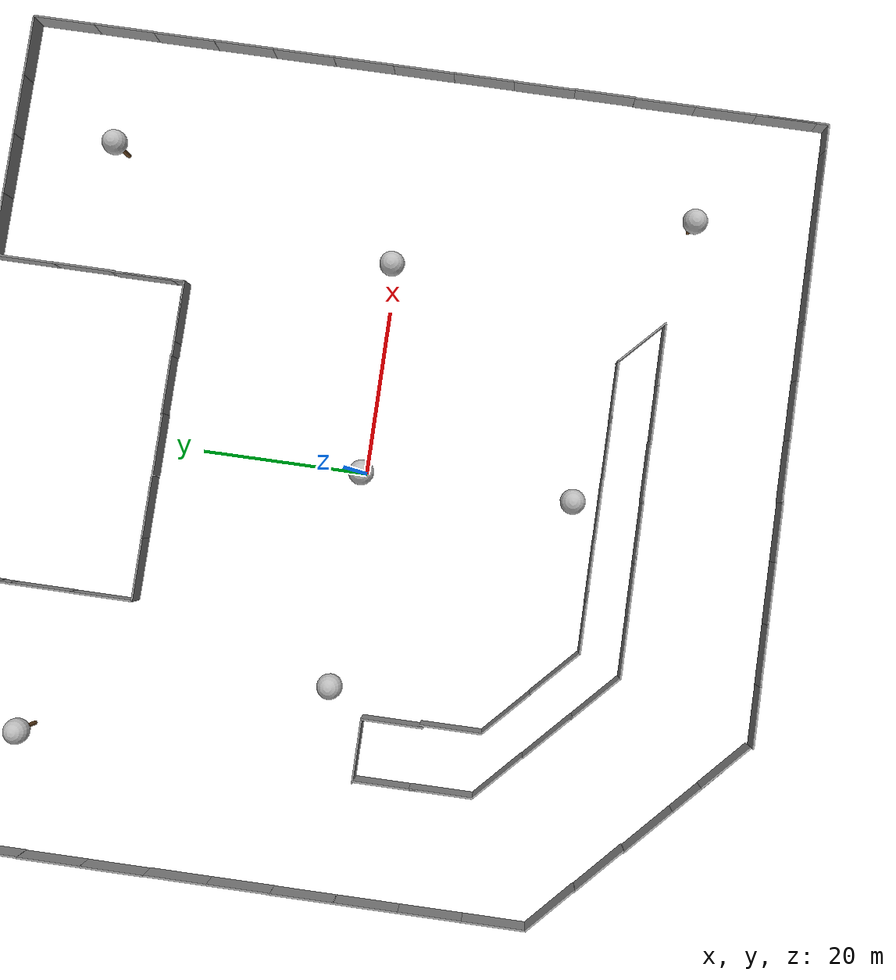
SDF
<sdf version="1.6">
 <world name="default">
  <plugin name="mrs_gazebo_static_transform_republisher_plugin" filename="libMRSGazeboStaticTransformRepublisher.so"/>
  <spherical_coordinates>
   <surface_model>EARTH_WGS84</surface_model>
   <latitude_deg>47.397743</latitude_deg>
   <longitude_deg>8.545594</longitude_deg>
   <elevation>0.0</elevation>
   <heading_deg>0</heading_deg>
  </spherical_coordinates>
  <physics name="default_physics" default="0" type="ode">
   <ode>
    <solver>
     <type>quick</type>
     <iters>10</iters>
     <sor>1.3</sor>
     <use_dynamic_moi_rescaling>0</use_dynamic_moi_rescaling>
    </solver>
    <constraints>
     <cfm>0</cfm>
     <erp>0.2</erp>
     <contact_max_correcting_vel>1000</contact_max_correcting_vel>
     <contact_surface_layer>0.001</contact_surface_layer>
    </constraints>
   </ode>
   <max_step_size>0.004</max_step_size>
   <real_time_factor>1</real_time_factor>
   <real_time_update_rate>250</real_time_update_rate>
  </physics>
  <scene><shadows>false</shadows></scene>
  <light type="directional" name="sun">
   <pose>250 250 600 0 0 0</pose>
   <diffuse>0.8 0.8 0.8 1</diffuse>
   <specular>0.2 0.2 0.2 1</specular>
   <attenuation>
    <range>1000</range>
    <constant>0.9</constant>
    <linear>0.01</linear>
    <quadratic>0.001</quadratic>
   </attenuation>
   <direction>0 0 -1</direction>
  </light>
  <model name="the_void">
   <static>1</static>
   <link name="link">
    <pose>0 0 0.1 0 -0 0</pose>
    <visual name="the_void">
     <pose>0 0 2 0 -0 0</pose>
     <geometry><sphere><radius>0.25</radius></sphere></geometry>
     <material>
      <script><uri>file://media/materials/scripts/Gazebo.material</uri><name>Gazebo/Black</name></script>
     </material>
    </visual>
   </link>
   <pose>-1000 -1000 0 0 -0 0</pose>
  </model>
  <plugin name="rviz_cam_synchronizer" filename="librviz_cam_synchronizer.so">
   <target_frame_id>gazebo_user_camera</target_frame_id>
   <world_origin_frame_id>uav1/gps_origin</world_origin_frame_id>
   <gazebo_camera_pose_topic>~/user_camera/pose</gazebo_camera_pose_topic>
   <target_frame_id>uav1::base_link</target_frame_id>
  </plugin>
  <gravity>0 0 -9.8066</gravity>
  <magnetic_field>6e-06 2.3e-05 -4.2e-05</magnetic_field>
  <atmosphere type="adiabatic"/>
  <model name="grey_wall">
   <static>1</static>
   <link name="link">
    <pose>0 0 1.4 0 -0 0</pose>
    <collision name="collision"><geometry><box><size>7.5 0.2 2.8</size></box></geometry></collision>
    <visual name="visual">
     <cast_shadows>0</cast_shadows>
     <geometry><box><size>7.5 0.2 2.8</size></box></geometry>
     <material>
      <script>
       <uri>model://grey_wall/materials/scripts</uri>
       <uri>model://grey_wall/materials/textures</uri>
       <name>vrc/grey_wall</name>
      </script>
     </material>
    </visual>
   </link>
   <pose>0 -50 0 0 -0 0</pose>
  </model>
  <model name="grey_wall_0">
   <static>1</static>
   <link name="link">
    <pose>0 0 1.4 0 -0 0</pose>
    <collision name="collision"><geometry><box><size>7.5 0.2 2.8</size></box></geometry></collision>
    <visual name="visual">
     <cast_shadows>0</cast_shadows>
     <geometry><box><size>7.5 0.2 2.8</size></box></geometry>
     <material>
      <script>
       <uri>model://grey_wall/materials/scripts</uri>
       <uri>model://grey_wall/materials/textures</uri>
       <name>vrc/grey_wall</name>
      </script>
     </material>
    </visual>
   </link>
   <pose>0 25 0 0 -0 0</pose>
  </model>
  <model name="grey_wall_1">
   <static>1</static>
   <link name="link">
    <pose>0 0 1.4 0 -0 0</pose>
    <collision name="collision"><geometry><box><size>7.5 0.2 2.8</size></box></geometry></collision>
    <visual name="visual">
     <cast_shadows>0</cast_shadows>
     <geometry><box><size>7.5 0.2 2.8</size></box></geometry>
     <material>
      <script>
       <uri>model://grey_wall/materials/scripts</uri>
       <uri>model://grey_wall/materials/textures</uri>
       <name>vrc/grey_wall</name>
      </script>
     </material>
    </visual>
   </link>
   <pose>50 0 0 0 -0 1.57</pose>
  </model>
  <model name="grey_wall_1_clone">
   <static>1</static>
   <link name="link">
    <pose>0 0 1.4 0 -0 0</pose>
    <collision name="collision"><geometry><box><size>7.5 0.2 2.8</size></box></geometry></collision>
    <visual name="visual">
     <cast_shadows>0</cast_shadows>
     <geometry><box><size>7.5 0.2 2.8</size></box></geometry>
     <material>
      <script>
       <uri>model://grey_wall/materials/scripts</uri>
       <uri>model://grey_wall/materials/textures</uri>
       <name>vrc/grey_wall</name>
      </script>
     </material>
    </visual>
   </link>
   <pose>-50 0 0 0 -0 1.57</pose>
  </model>
  <model name="grey_wall_1_clone_clone">
   <static>1</static>
   <link name="link">
    <pose>0 0 1.4 0 -0 0</pose>
    <collision name="collision"><geometry><box><size>7.5 0.2 2.8</size></box></geometry></collision>
    <visual name="visual">
     <cast_shadows>0</cast_shadows>
     <geometry><box><size>7.5 0.2 2.8</size></box></geometry>
     <material>
      <script>
       <uri>model://grey_wall/materials/scripts</uri>
       <uri>model://grey_wall/materials/textures</uri>
       <name>vrc/grey_wall</name>
      </script>
     </material>
    </visual>
   </link>
   <pose>-50.0069 -7.58109 0 0 -0 1.57</pose>
  </model>
  <model name="grey_wall_1_clone_clone_0">
   <static>1</static>
   <link name="link">
    <pose>0 0 1.4 0 -0 0</pose>
    <collision name="collision"><geometry><box><size>7.5 0.2 2.8</size></box></geometry></collision>
    <visual name="visual">
     <cast_shadows>0</cast_shadows>
     <geometry><box><size>7.5 0.2 2.8</size></box></geometry>
     <material>
      <script>
       <uri>model://grey_wall/materials/scripts</uri>
       <uri>model://grey_wall/materials/textures</uri>
       <name>vrc/grey_wall</name>
      </script>
     </material>
    </visual>
   </link>
   <pose>-50.0101 -15.0734 0 0 -0 1.57</pose>
  </model>
  <model name="grey_wall_1_clone_clone_1">
   <static>1</static>
   <link name="link">
    <pose>0 0 1.4 0 -0 0</pose>
    <collision name="collision"><geometry><box><size>7.5 0.2 2.8</size></box></geometry></collision>
    <visual name="visual">
     <cast_shadows>0</cast_shadows>
     <geometry><box><size>7.5 0.2 2.8</size></box></geometry>
     <material>
      <script>
       <uri>model://grey_wall/materials/scripts</uri>
       <uri>model://grey_wall/materials/textures</uri>
       <name>vrc/grey_wall</name>
      </script>
     </material>
    </visual>
   </link>
   <pose>-50.0164 -22.5285 0 0 -0 1.57</pose>
  </model>
  <model name="grey_wall_1_clone_clone_5">
   <static>1</static>
   <link name="link">
    <pose>0 0 1.4 0 -0 0</pose>
    <collision name="collision"><geometry><box><size>7.5 0.2 2.8</size></box></geometry></collision>
    <visual name="visual">
     <cast_shadows>0</cast_shadows>
     <geometry><box><size>7.5 0.2 2.8</size></box></geometry>
     <material>
      <script>
       <uri>model://grey_wall/materials/scripts</uri>
       <uri>model://grey_wall/materials/textures</uri>
       <name>vrc/grey_wall</name>
      </script>
     </material>
    </visual>
   </link>
   <pose>-49.9698 7.44842 0 0 -0 1.57</pose>
  </model>
  <model name="grey_wall_1_clone_clone_6">
   <static>1</static>
   <link name="link">
    <pose>0 0 1.4 0 -0 0</pose>
    <collision name="collision"><geometry><box><size>7.5 0.2 2.8</size></box></geometry></collision>
    <visual name="visual">
     <cast_shadows>0</cast_shadows>
     <geometry><box><size>7.5 0.2 2.8</size></box></geometry>
     <material>
      <script>
       <uri>model://grey_wall/materials/scripts</uri>
       <uri>model://grey_wall/materials/textures</uri>
       <name>vrc/grey_wall</name>
      </script>
     </material>
    </visual>
   </link>
   <pose>-49.9652 14.8689 0 0 -0 1.57</pose>
  </model>
  <model name="grey_wall_1_clone_clone_7">
   <static>1</static>
   <link name="link">
    <pose>0 0 1.4 0 -0 0</pose>
    <collision name="collision"><geometry><box><size>7.5 0.2 2.8</size></box></geometry></collision>
    <visual name="visual">
     <cast_shadows>0</cast_shadows>
     <geometry><box><size>7.5 0.2 2.8</size></box></geometry>
     <material>
      <script>
       <uri>model://grey_wall/materials/scripts</uri>
       <uri>model://grey_wall/materials/textures</uri>
       <name>vrc/grey_wall</name>
      </script>
     </material>
    </visual>
   </link>
   <pose>-49.9949 22.3819 0 0 -0 1.57</pose>
  </model>
  <model name="grey_wall_1_clone_clone_8">
   <static>1</static>
   <link name="link">
    <pose>0 0 1.4 0 -0 0</pose>
    <collision name="collision"><geometry><box><size>7.5 0.2 2.8</size></box></geometry></collision>
    <visual name="visual">
     <cast_shadows>0</cast_shadows>
     <geometry><box><size>7.5 0.2 2.8</size></box></geometry>
     <material>
      <script>
       <uri>model://grey_wall/materials/scripts</uri>
       <uri>model://grey_wall/materials/textures</uri>
       <name>vrc/grey_wall</name>
      </script>
     </material>
    </visual>
   </link>
   <pose>-49.9767 29.8462 0 0 -0 1.57</pose>
  </model>
  <model name="grey_wall_1_clone_clone_9">
   <static>1</static>
   <link name="link">
    <pose>0 0 1.4 0 -0 0</pose>
    <collision name="collision"><geometry><box><size>7.5 0.2 2.8</size></box></geometry></collision>
    <visual name="visual">
     <cast_shadows>0</cast_shadows>
     <geometry><box><size>7.5 0.2 2.8</size></box></geometry>
     <material>
      <script>
       <uri>model://grey_wall/materials/scripts</uri>
       <uri>model://grey_wall/materials/textures</uri>
       <name>vrc/grey_wall</name>
      </script>
     </material>
    </visual>
   </link>
   <pose>-49.9236 37.2825 0 0 -0 1.57</pose>
  </model>
  <model name="grey_wall_1_clone_clone_10">
   <static>1</static>
   <link name="link">
    <pose>0 0 1.4 0 -0 0</pose>
    <collision name="collision"><geometry><box><size>7.5 0.2 2.8</size></box></geometry></collision>
    <visual name="visual">
     <cast_shadows>0</cast_shadows>
     <geometry><box><size>7.5 0.2 2.8</size></box></geometry>
     <material>
      <script>
       <uri>model://grey_wall/materials/scripts</uri>
       <uri>model://grey_wall/materials/textures</uri>
       <name>vrc/grey_wall</name>
      </script>
     </material>
    </visual>
   </link>
   <pose>-49.9256 44.774 0 0 -0 1.57</pose>
  </model>
  <model name="grey_wall_1_clone_clone_11">
   <static>1</static>
   <link name="link">
    <pose>0 0 1.4 0 -0 0</pose>
    <collision name="collision"><geometry><box><size>7.5 0.2 2.8</size></box></geometry></collision>
    <visual name="visual">
     <cast_shadows>0</cast_shadows>
     <geometry><box><size>7.5 0.2 2.8</size></box></geometry>
     <material>
      <script>
       <uri>model://grey_wall/materials/scripts</uri>
       <uri>model://grey_wall/materials/textures</uri>
       <name>vrc/grey_wall</name>
      </script>
     </material>
    </visual>
   </link>
   <pose>50.0103 -7.49568 0 0 -0 1.57</pose>
  </model>
  <model name="grey_wall_1_clone_clone_12">
   <static>1</static>
   <link name="link">
    <pose>0 0 1.4 0 -0 0</pose>
    <collision name="collision"><geometry><box><size>7.5 0.2 2.8</size></box></geometry></collision>
    <visual name="visual">
     <cast_shadows>0</cast_shadows>
     <geometry><box><size>7.5 0.2 2.8</size></box></geometry>
     <material>
      <script>
       <uri>model://grey_wall/materials/scripts</uri>
       <uri>model://grey_wall/materials/textures</uri>
       <name>vrc/grey_wall</name>
      </script>
     </material>
    </visual>
   </link>
   <pose>49.9783 -15.0116 0 0 -0 1.57</pose>
  </model>
  <model name="grey_wall_1_clone_clone_13">
   <static>1</static>
   <link name="link">
    <pose>0 0 1.4 0 -0 0</pose>
    <collision name="collision"><geometry><box><size>7.5 0.2 2.8</size></box></geometry></collision>
    <visual name="visual">
     <cast_shadows>0</cast_shadows>
     <geometry><box><size>7.5 0.2 2.8</size></box></geometry>
     <material>
      <script>
       <uri>model://grey_wall/materials/scripts</uri>
       <uri>model://grey_wall/materials/textures</uri>
       <name>vrc/grey_wall</name>
      </script>
     </material>
    </visual>
   </link>
   <pose>50.0236 -22.4733 0 0 -0 1.57</pose>
  </model>
  <model name="grey_wall_1_clone_clone_14">
   <static>1</static>
   <link name="link">
    <pose>0 0 1.4 0 -0 0</pose>
    <collision name="collision"><geometry><box><size>7.5 0.2 2.8</size></box></geometry></collision>
    <visual name="visual">
     <cast_shadows>0</cast_shadows>
     <geometry><box><size>7.5 0.2 2.8</size></box></geometry>
     <material>
      <script>
       <uri>model://grey_wall/materials/scripts</uri>
       <uri>model://grey_wall/materials/textures</uri>
       <name>vrc/grey_wall</name>
      </script>
     </material>
    </visual>
   </link>
   <pose>49.9472 -29.9173 0 0 -0 1.57</pose>
  </model>
  <model name="grey_wall_1_clone_clone_15">
   <static>1</static>
   <link name="link">
    <pose>0 0 1.4 0 -0 0</pose>
    <collision name="collision"><geometry><box><size>7.5 0.2 2.8</size></box></geometry></collision>
    <visual name="visual">
     <cast_shadows>0</cast_shadows>
     <geometry><box><size>7.5 0.2 2.8</size></box></geometry>
     <material>
      <script>
       <uri>model://grey_wall/materials/scripts</uri>
       <uri>model://grey_wall/materials/textures</uri>
       <name>vrc/grey_wall</name>
      </script>
     </material>
    </visual>
   </link>
   <pose>49.9295 -37.3932 0 0 -0 1.57</pose>
  </model>
  <model name="grey_wall_1_clone_clone_16">
   <static>1</static>
   <link name="link">
    <pose>0 0 1.4 0 -0 0</pose>
    <collision name="collision"><geometry><box><size>7.5 0.2 2.8</size></box></geometry></collision>
    <visual name="visual">
     <cast_shadows>0</cast_shadows>
     <geometry><box><size>7.5 0.2 2.8</size></box></geometry>
     <material>
      <script>
       <uri>model://grey_wall/materials/scripts</uri>
       <uri>model://grey_wall/materials/textures</uri>
       <name>vrc/grey_wall</name>
      </script>
     </material>
    </visual>
   </link>
   <pose>49.9377 -44.8561 0 0 -0 1.57</pose>
  </model>
  <model name="grey_wall_1_clone_clone_17">
   <static>1</static>
   <link name="link">
    <pose>0 0 1.4 0 -0 0</pose>
    <collision name="collision"><geometry><box><size>7.5 0.2 2.8</size></box></geometry></collision>
    <visual name="visual">
     <cast_shadows>0</cast_shadows>
     <geometry><box><size>7.5 0.2 2.8</size></box></geometry>
     <material>
      <script>
       <uri>model://grey_wall/materials/scripts</uri>
       <uri>model://grey_wall/materials/textures</uri>
       <name>vrc/grey_wall</name>
      </script>
     </material>
    </visual>
   </link>
   <pose>50.0095 7.49254 0 0 -0 1.57</pose>
  </model>
  <model name="grey_wall_1_clone_clone_18">
   <static>1</static>
   <link name="link">
    <pose>0 0 1.4 0 -0 0</pose>
    <collision name="collision"><geometry><box><size>7.5 0.2 2.8</size></box></geometry></collision>
    <visual name="visual">
     <cast_shadows>0</cast_shadows>
     <geometry><box><size>7.5 0.2 2.8</size></box></geometry>
     <material>
      <script>
       <uri>model://grey_wall/materials/scripts</uri>
       <uri>model://grey_wall/materials/textures</uri>
       <name>vrc/grey_wall</name>
      </script>
     </material>
    </visual>
   </link>
   <pose>50.0062 14.9242 0 0 -0 1.57</pose>
  </model>
  <model name="grey_wall_1_clone_clone_19">
   <static>1</static>
   <link name="link">
    <pose>0 0 1.4 0 -0 0</pose>
    <collision name="collision"><geometry><box><size>7.5 0.2 2.8</size></box></geometry></collision>
    <visual name="visual">
     <cast_shadows>0</cast_shadows>
     <geometry><box><size>7.5 0.2 2.8</size></box></geometry>
     <material>
      <script>
       <uri>model://grey_wall/materials/scripts</uri>
       <uri>model://grey_wall/materials/textures</uri>
       <name>vrc/grey_wall</name>
      </script>
     </material>
    </visual>
   </link>
   <pose>50.0246 22.3183 0 0 -0 1.57</pose>
  </model>
  <model name="grey_wall_1_clone_clone_20">
   <static>1</static>
   <link name="link">
    <pose>0 0 1.4 0 -0 0</pose>
    <collision name="collision"><geometry><box><size>7.5 0.2 2.8</size></box></geometry></collision>
    <visual name="visual">
     <cast_shadows>0</cast_shadows>
     <geometry><box><size>7.5 0.2 2.8</size></box></geometry>
     <material>
      <script>
       <uri>model://grey_wall/materials/scripts</uri>
       <uri>model://grey_wall/materials/textures</uri>
       <name>vrc/grey_wall</name>
      </script>
     </material>
    </visual>
   </link>
   <pose>50.0134 29.75 0 0 -0 1.57</pose>
  </model>
  <model name="grey_wall_1_clone_clone_21">
   <static>1</static>
   <link name="link">
    <pose>0 0 1.4 0 -0 0</pose>
    <collision name="collision"><geometry><box><size>7.5 0.2 2.8</size></box></geometry></collision>
    <visual name="visual">
     <cast_shadows>0</cast_shadows>
     <geometry><box><size>7.5 0.2 2.8</size></box></geometry>
     <material>
      <script>
       <uri>model://grey_wall/materials/scripts</uri>
       <uri>model://grey_wall/materials/textures</uri>
       <name>vrc/grey_wall</name>
      </script>
     </material>
    </visual>
   </link>
   <pose>50.0432 37.227 0 0 -0 1.57</pose>
  </model>
  <model name="grey_wall_1_clone_clone_22">
   <static>1</static>
   <link name="link">
    <pose>0 0 1.4 0 -0 0</pose>
    <collision name="collision"><geometry><box><size>7.5 0.2 2.8</size></box></geometry></collision>
    <visual name="visual">
     <cast_shadows>0</cast_shadows>
     <geometry><box><size>7.5 0.2 2.8</size></box></geometry>
     <material>
      <script>
       <uri>model://grey_wall/materials/scripts</uri>
       <uri>model://grey_wall/materials/textures</uri>
       <name>vrc/grey_wall</name>
      </script>
     </material>
    </visual>
   </link>
   <pose>50.0462 44.6648 0 0 -0 1.57</pose>
  </model>
  <model name="grey_wall_0_clone">
   <static>1</static>
   <link name="link">
    <pose>0 0 1.4 0 -0 0</pose>
    <collision name="collision"><geometry><box><size>7.5 0.2 2.8</size></box></geometry></collision>
    <visual name="visual">
     <cast_shadows>0</cast_shadows>
     <geometry><box><size>7.5 0.2 2.8</size></box></geometry>
     <material>
      <script>
       <uri>model://grey_wall/materials/scripts</uri>
       <uri>model://grey_wall/materials/textures</uri>
       <name>vrc/grey_wall</name>
      </script>
     </material>
    </visual>
   </link>
   <pose>7.24673 25.0713 0 0 -0 0</pose>
  </model>
  <model name="grey_wall_0_clone_0">
   <static>1</static>
   <link name="link">
    <pose>0 0 1.4 0 -0 0</pose>
    <collision name="collision"><geometry><box><size>7.5 0.2 2.8</size></box></geometry></collision>
    <visual name="visual">
     <cast_shadows>0</cast_shadows>
     <geometry><box><size>7.5 0.2 2.8</size></box></geometry>
     <material>
      <script>
       <uri>model://grey_wall/materials/scripts</uri>
       <uri>model://grey_wall/materials/textures</uri>
       <name>vrc/grey_wall</name>
      </script>
     </material>
    </visual>
   </link>
   <pose>14.524 24.9801 0 0 -0 0</pose>
  </model>
  <model name="grey_wall_0_clone_1">
   <static>1</static>
   <link name="link">
    <pose>0 0 1.4 0 -0 0</pose>
    <collision name="collision"><geometry><box><size>7.5 0.2 2.8</size></box></geometry></collision>
    <visual name="visual">
     <cast_shadows>0</cast_shadows>
     <geometry><box><size>7.5 0.2 2.8</size></box></geometry>
     <material>
      <script>
       <uri>model://grey_wall/materials/scripts</uri>
       <uri>model://grey_wall/materials/textures</uri>
       <name>vrc/grey_wall</name>
      </script>
     </material>
    </visual>
   </link>
   <pose>-7.57341 25.0553 0 0 -0 0</pose>
  </model>
  <model name="grey_wall_0_clone_2">
   <static>1</static>
   <link name="link">
    <pose>0 0 1.4 0 -0 0</pose>
    <collision name="collision"><geometry><box><size>7.5 0.2 2.8</size></box></geometry></collision>
    <visual name="visual">
     <cast_shadows>0</cast_shadows>
     <geometry><box><size>7.5 0.2 2.8</size></box></geometry>
     <material>
      <script>
       <uri>model://grey_wall/materials/scripts</uri>
       <uri>model://grey_wall/materials/textures</uri>
       <name>vrc/grey_wall</name>
      </script>
     </material>
    </visual>
   </link>
   <pose>-15.0654 25.055 0 0 -0 0</pose>
  </model>
  <model name="grey_wall_0_clone_3">
   <static>1</static>
   <link name="link">
    <pose>0 0 1.4 0 -0 0</pose>
    <collision name="collision"><geometry><box><size>7.5 0.2 2.8</size></box></geometry></collision>
    <visual name="visual">
     <cast_shadows>0</cast_shadows>
     <geometry><box><size>7.5 0.2 2.8</size></box></geometry>
     <material>
      <script>
       <uri>model://grey_wall/materials/scripts</uri>
       <uri>model://grey_wall/materials/textures</uri>
       <name>vrc/grey_wall</name>
      </script>
     </material>
    </visual>
   </link>
   <pose>46.2788 48.4572 0 0 -0 0</pose>
  </model>
  <model name="grey_wall_0_clone_4">
   <static>1</static>
   <link name="link">
    <pose>0 0 1.4 0 -0 0</pose>
    <collision name="collision"><geometry><box><size>7.5 0.2 2.8</size></box></geometry></collision>
    <visual name="visual">
     <cast_shadows>0</cast_shadows>
     <geometry><box><size>7.5 0.2 2.8</size></box></geometry>
     <material>
      <script>
       <uri>model://grey_wall/materials/scripts</uri>
       <uri>model://grey_wall/materials/textures</uri>
       <name>vrc/grey_wall</name>
      </script>
     </material>
    </visual>
   </link>
   <pose>38.8606 48.4742 0 0 -0 0</pose>
  </model>
  <model name="grey_wall_0_clone_5">
   <static>1</static>
   <link name="link">
    <pose>0 0 1.4 0 -0 0</pose>
    <collision name="collision"><geometry><box><size>7.5 0.2 2.8</size></box></geometry></collision>
    <visual name="visual">
     <cast_shadows>0</cast_shadows>
     <geometry><box><size>7.5 0.2 2.8</size></box></geometry>
     <material>
      <script>
       <uri>model://grey_wall/materials/scripts</uri>
       <uri>model://grey_wall/materials/textures</uri>
       <name>vrc/grey_wall</name>
      </script>
     </material>
    </visual>
   </link>
   <pose>31.4054 48.4637 0 0 -0 0</pose>
  </model>
  <model name="grey_wall_0_clone_6">
   <static>1</static>
   <link name="link">
    <pose>0 0 1.4 0 -0 0</pose>
    <collision name="collision"><geometry><box><size>7.5 0.2 2.8</size></box></geometry></collision>
    <visual name="visual">
     <cast_shadows>0</cast_shadows>
     <geometry><box><size>7.5 0.2 2.8</size></box></geometry>
     <material>
      <script>
       <uri>model://grey_wall/materials/scripts</uri>
       <uri>model://grey_wall/materials/textures</uri>
       <name>vrc/grey_wall</name>
      </script>
     </material>
    </visual>
   </link>
   <pose>23.9127 48.4733 0 0 -0 0</pose>
  </model>
  <model name="grey_wall_1_clone_clone_22_clone">
   <static>1</static>
   <link name="link">
    <pose>0 0 1.4 0 -0 0</pose>
    <collision name="collision"><geometry><box><size>7.5 0.2 2.8</size></box></geometry></collision>
    <visual name="visual">
     <cast_shadows>0</cast_shadows>
     <geometry><box><size>7.5 0.2 2.8</size></box></geometry>
     <material>
      <script>
       <uri>model://grey_wall/materials/scripts</uri>
       <uri>model://grey_wall/materials/textures</uri>
       <name>vrc/grey_wall</name>
      </script>
     </material>
    </visual>
   </link>
   <pose>20.0153 44.7619 0 0 -0 1.57</pose>
  </model>
  <model name="grey_wall_1_clone_clone_22_clone_0">
   <static>1</static>
   <link name="link">
    <pose>0 0 1.4 0 -0 0</pose>
    <collision name="collision"><geometry><box><size>7.5 0.2 2.8</size></box></geometry></collision>
    <visual name="visual">
     <cast_shadows>0</cast_shadows>
     <geometry><box><size>7.5 0.2 2.8</size></box></geometry>
     <material>
      <script>
       <uri>model://grey_wall/materials/scripts</uri>
       <uri>model://grey_wall/materials/textures</uri>
       <name>vrc/grey_wall</name>
      </script>
     </material>
    </visual>
   </link>
   <pose>20.0236 37.279 0 0 -0 1.57</pose>
  </model>
  <model name="grey_wall_1_clone_clone_22_clone_1">
   <static>1</static>
   <link name="link">
    <pose>0 0 1.4 0 -0 0</pose>
    <collision name="collision"><geometry><box><size>7.5 0.2 2.8</size></box></geometry></collision>
    <visual name="visual">
     <cast_shadows>0</cast_shadows>
     <geometry><box><size>7.5 0.2 2.8</size></box></geometry>
     <material>
      <script>
       <uri>model://grey_wall/materials/scripts</uri>
       <uri>model://grey_wall/materials/textures</uri>
       <name>vrc/grey_wall</name>
      </script>
     </material>
    </visual>
   </link>
   <pose>19.9294 30.0842 0 0 -0 1.57</pose>
  </model>
  <model name="grey_wall_1_clone_clone_22_clone_2">
   <static>1</static>
   <link name="link">
    <pose>0 0 1.4 0 -0 0</pose>
    <collision name="collision"><geometry><box><size>7.5 0.2 2.8</size></box></geometry></collision>
    <visual name="visual">
     <cast_shadows>0</cast_shadows>
     <geometry><box><size>7.5 0.2 2.8</size></box></geometry>
     <material>
      <script>
       <uri>model://grey_wall/materials/scripts</uri>
       <uri>model://grey_wall/materials/textures</uri>
       <name>vrc/grey_wall</name>
      </script>
     </material>
    </visual>
   </link>
   <pose>19.9494 28.6505 0 0 -0 1.57</pose>
  </model>
  <model name="grey_wall_0_clone_0_clone">
   <static>1</static>
   <link name="link">
    <pose>0 0 1.4 0 -0 0</pose>
    <collision name="collision"><geometry><box><size>7.5 0.2 2.8</size></box></geometry></collision>
    <visual name="visual">
     <cast_shadows>0</cast_shadows>
     <geometry><box><size>7.5 0.2 2.8</size></box></geometry>
     <material>
      <script>
       <uri>model://grey_wall/materials/scripts</uri>
       <uri>model://grey_wall/materials/textures</uri>
       <name>vrc/grey_wall</name>
      </script>
     </material>
    </visual>
   </link>
   <pose>16.3024 24.9572 0 0 -0 0</pose>
  </model>
  <model name="grey_wall_0_clone_0_clone_0">
   <static>1</static>
   <link name="link">
    <pose>0 0 1.4 0 -0 0</pose>
    <collision name="collision"><geometry><box><size>7.5 0.2 2.8</size></box></geometry></collision>
    <visual name="visual">
     <cast_shadows>0</cast_shadows>
     <geometry><box><size>7.5 0.2 2.8</size></box></geometry>
     <material>
      <script>
       <uri>model://grey_wall/materials/scripts</uri>
       <uri>model://grey_wall/materials/textures</uri>
       <name>vrc/grey_wall</name>
      </script>
     </material>
    </visual>
   </link>
   <pose>-46.3147 48.5898 0 0 -0 0</pose>
  </model>
  <model name="grey_wall_0_clone_0_clone_1">
   <static>1</static>
   <link name="link">
    <pose>0 0 1.4 0 -0 0</pose>
    <collision name="collision"><geometry><box><size>7.5 0.2 2.8</size></box></geometry></collision>
    <visual name="visual">
     <cast_shadows>0</cast_shadows>
     <geometry><box><size>7.5 0.2 2.8</size></box></geometry>
     <material>
      <script>
       <uri>model://grey_wall/materials/scripts</uri>
       <uri>model://grey_wall/materials/textures</uri>
       <name>vrc/grey_wall</name>
      </script>
     </material>
    </visual>
   </link>
   <pose>-39.2009 48.6375 0 0 -0 0</pose>
  </model>
  <model name="grey_wall_0_clone_0_clone_2">
   <static>1</static>
   <link name="link">
    <pose>0 0 1.4 0 -0 0</pose>
    <collision name="collision"><geometry><box><size>7.5 0.2 2.8</size></box></geometry></collision>
    <visual name="visual">
     <cast_shadows>0</cast_shadows>
     <geometry><box><size>7.5 0.2 2.8</size></box></geometry>
     <material>
      <script>
       <uri>model://grey_wall/materials/scripts</uri>
       <uri>model://grey_wall/materials/textures</uri>
       <name>vrc/grey_wall</name>
      </script>
     </material>
    </visual>
   </link>
   <pose>-32.1036 48.6414 0 0 -0 0</pose>
  </model>
  <model name="grey_wall_0_clone_0_clone_3">
   <static>1</static>
   <link name="link">
    <pose>0 0 1.4 0 -0 0</pose>
    <collision name="collision"><geometry><box><size>7.5 0.2 2.8</size></box></geometry></collision>
    <visual name="visual">
     <cast_shadows>0</cast_shadows>
     <geometry><box><size>7.5 0.2 2.8</size></box></geometry>
     <material>
      <script>
       <uri>model://grey_wall/materials/scripts</uri>
       <uri>model://grey_wall/materials/textures</uri>
       <name>vrc/grey_wall</name>
      </script>
     </material>
    </visual>
   </link>
   <pose>-24.918 48.6507 0 0 -0 0</pose>
  </model>
  <model name="grey_wall_1_clone_clone_22_clone_0_clone">
   <static>1</static>
   <link name="link">
    <pose>0 0 1.4 0 -0 0</pose>
    <collision name="collision"><geometry><box><size>7.5 0.2 2.8</size></box></geometry></collision>
    <visual name="visual">
     <cast_shadows>0</cast_shadows>
     <geometry><box><size>7.5 0.2 2.8</size></box></geometry>
     <material>
      <script>
       <uri>model://grey_wall/materials/scripts</uri>
       <uri>model://grey_wall/materials/textures</uri>
       <name>vrc/grey_wall</name>
      </script>
     </material>
    </visual>
   </link>
   <pose>-18.8003 28.7492 0 0 -0 1.57</pose>
  </model>
  <model name="grey_wall_1_clone_clone_22_clone_0_clone_0">
   <static>1</static>
   <link name="link">
    <pose>0 0 1.4 0 -0 0</pose>
    <collision name="collision"><geometry><box><size>7.5 0.2 2.8</size></box></geometry></collision>
    <visual name="visual">
     <cast_shadows>0</cast_shadows>
     <geometry><box><size>7.5 0.2 2.8</size></box></geometry>
     <material>
      <script>
       <uri>model://grey_wall/materials/scripts</uri>
       <uri>model://grey_wall/materials/textures</uri>
       <name>vrc/grey_wall</name>
      </script>
     </material>
    </visual>
   </link>
   <pose>-18.7629 36.234 0 0 -0 1.57</pose>
  </model>
  <model name="grey_wall_1_clone_clone_22_clone_0_clone_1">
   <static>1</static>
   <link name="link">
    <pose>0 0 1.4 0 -0 0</pose>
    <collision name="collision"><geometry><box><size>7.5 0.2 2.8</size></box></geometry></collision>
    <visual name="visual">
     <cast_shadows>0</cast_shadows>
     <geometry><box><size>7.5 0.2 2.8</size></box></geometry>
     <material>
      <script>
       <uri>model://grey_wall/materials/scripts</uri>
       <uri>model://grey_wall/materials/textures</uri>
       <name>vrc/grey_wall</name>
      </script>
     </material>
    </visual>
   </link>
   <pose>-18.7362 43.586 0 0 -0 1.57</pose>
  </model>
  <model name="grey_wall_1_clone_clone_22_clone_0_clone_2">
   <static>1</static>
   <link name="link">
    <pose>0 0 1.4 0 -0 0</pose>
    <collision name="collision"><geometry><box><size>7.5 0.2 2.8</size></box></geometry></collision>
    <visual name="visual">
     <cast_shadows>0</cast_shadows>
     <geometry><box><size>7.5 0.2 2.8</size></box></geometry>
     <material>
      <script>
       <uri>model://grey_wall/materials/scripts</uri>
       <uri>model://grey_wall/materials/textures</uri>
       <name>vrc/grey_wall</name>
      </script>
     </material>
    </visual>
   </link>
   <pose>-18.6991 45.0127 0 0 -0 1.57</pose>
  </model>
  <model name="grey_wall_0_clone_0_clone_3_clone">
   <static>1</static>
   <link name="link">
    <pose>0 0 1.4 0 -0 0</pose>
    <collision name="collision"><geometry><box><size>7.5 0.2 2.8</size></box></geometry></collision>
    <visual name="visual">
     <cast_shadows>0</cast_shadows>
     <geometry><box><size>7.5 0.2 2.8</size></box></geometry>
     <material>
      <script>
       <uri>model://grey_wall/materials/scripts</uri>
       <uri>model://grey_wall/materials/textures</uri>
       <name>vrc/grey_wall</name>
      </script>
     </material>
    </visual>
   </link>
   <pose>-22.4187 48.6445 0 0 -0 0</pose>
  </model>
  <model name="grey_wall_1_clone_clone_1_clone">
   <static>1</static>
   <link name="link">
    <pose>0 0 1.4 0 -0 0</pose>
    <collision name="collision"><geometry><box><size>7.5 0.2 2.8</size></box></geometry></collision>
    <visual name="visual">
     <cast_shadows>0</cast_shadows>
     <geometry><box><size>7.5 0.2 2.8</size></box></geometry>
     <material>
      <script>
       <uri>model://grey_wall/materials/scripts</uri>
       <uri>model://grey_wall/materials/textures</uri>
       <name>vrc/grey_wall</name>
      </script>
     </material>
    </visual>
   </link>
   <pose>-47.3725 -28.8757 0 0 0 -0.76</pose>
  </model>
  <model name="grey_wall_1_clone_clone_1_clone_clone">
   <static>1</static>
   <link name="link">
    <pose>0 0 1.4 0 -0 0</pose>
    <collision name="collision"><geometry><box><size>7.5 0.2 2.8</size></box></geometry></collision>
    <visual name="visual">
     <cast_shadows>0</cast_shadows>
     <geometry><box><size>7.5 0.2 2.8</size></box></geometry>
     <material>
      <script>
       <uri>model://grey_wall/materials/scripts</uri>
       <uri>model://grey_wall/materials/textures</uri>
       <name>vrc/grey_wall</name>
      </script>
     </material>
    </visual>
   </link>
   <pose>-42.1484 -33.9315 0 0 0 -0.76</pose>
  </model>
  <model name="grey_wall_1_clone_clone_1_clone_clone_0">
   <static>1</static>
   <link name="link">
    <pose>0 0 1.4 0 -0 0</pose>
    <collision name="collision"><geometry><box><size>7.5 0.2 2.8</size></box></geometry></collision>
    <visual name="visual">
     <cast_shadows>0</cast_shadows>
     <geometry><box><size>7.5 0.2 2.8</size></box></geometry>
     <material>
      <script>
       <uri>model://grey_wall/materials/scripts</uri>
       <uri>model://grey_wall/materials/textures</uri>
       <name>vrc/grey_wall</name>
      </script>
     </material>
    </visual>
   </link>
   <pose>-36.9662 -39.029 0 0 0 -0.76</pose>
  </model>
  <model name="grey_wall_1_clone_clone_1_clone_clone_1">
   <static>1</static>
   <link name="link">
    <pose>0 0 1.4 0 -0 0</pose>
    <collision name="collision"><geometry><box><size>7.5 0.2 2.8</size></box></geometry></collision>
    <visual name="visual">
     <cast_shadows>0</cast_shadows>
     <geometry><box><size>7.5 0.2 2.8</size></box></geometry>
     <material>
      <script>
       <uri>model://grey_wall/materials/scripts</uri>
       <uri>model://grey_wall/materials/textures</uri>
       <name>vrc/grey_wall</name>
      </script>
     </material>
    </visual>
   </link>
   <pose>-31.6772 -44.0599 0 0 0 -0.76</pose>
  </model>
  <model name="grey_wall_1_clone_clone_1_clone_clone_2">
   <static>1</static>
   <link name="link">
    <pose>0 0 1.4 0 -0 0</pose>
    <collision name="collision"><geometry><box><size>7.5 0.2 2.8</size></box></geometry></collision>
    <visual name="visual">
     <cast_shadows>0</cast_shadows>
     <geometry><box><size>7.5 0.2 2.8</size></box></geometry>
     <material>
      <script>
       <uri>model://grey_wall/materials/scripts</uri>
       <uri>model://grey_wall/materials/textures</uri>
       <name>vrc/grey_wall</name>
      </script>
     </material>
    </visual>
   </link>
   <pose>-28.376 -47.1636 0 0 0 -0.76</pose>
  </model>
  <model name="grey_wall_clone">
   <static>1</static>
   <link name="link">
    <pose>0 0 1.4 0 -0 0</pose>
    <collision name="collision"><geometry><box><size>7.5 0.2 2.8</size></box></geometry></collision>
    <visual name="visual">
     <cast_shadows>0</cast_shadows>
     <geometry><box><size>7.5 0.2 2.8</size></box></geometry>
     <material>
      <script>
       <uri>model://grey_wall/materials/scripts</uri>
       <uri>model://grey_wall/materials/textures</uri>
       <name>vrc/grey_wall</name>
      </script>
     </material>
    </visual>
   </link>
   <pose>-7.46873 -50.0037 0 0 -0 0</pose>
  </model>
  <model name="grey_wall_clone_0">
   <static>1</static>
   <link name="link">
    <pose>0 0 1.4 0 -0 0</pose>
    <collision name="collision"><geometry><box><size>7.5 0.2 2.8</size></box></geometry></collision>
    <visual name="visual">
     <cast_shadows>0</cast_shadows>
     <geometry><box><size>7.5 0.2 2.8</size></box></geometry>
     <material>
      <script>
       <uri>model://grey_wall/materials/scripts</uri>
       <uri>model://grey_wall/materials/textures</uri>
       <name>vrc/grey_wall</name>
      </script>
     </material>
    </visual>
   </link>
   <pose>-14.7709 -50.0132 0 0 -0 0</pose>
  </model>
  <model name="grey_wall_clone_1">
   <static>1</static>
   <link name="link">
    <pose>0 0 1.4 0 -0 0</pose>
    <collision name="collision"><geometry><box><size>7.5 0.2 2.8</size></box></geometry></collision>
    <visual name="visual">
     <cast_shadows>0</cast_shadows>
     <geometry><box><size>7.5 0.2 2.8</size></box></geometry>
     <material>
      <script>
       <uri>model://grey_wall/materials/scripts</uri>
       <uri>model://grey_wall/materials/textures</uri>
       <name>vrc/grey_wall</name>
      </script>
     </material>
    </visual>
   </link>
   <pose>-22.0179 -50.0306 0 0 -0 0</pose>
  </model>
  <model name="grey_wall_clone_2">
   <static>1</static>
   <link name="link">
    <pose>0 0 1.4 0 -0 0</pose>
    <collision name="collision"><geometry><box><size>7.5 0.2 2.8</size></box></geometry></collision>
    <visual name="visual">
     <cast_shadows>0</cast_shadows>
     <geometry><box><size>7.5 0.2 2.8</size></box></geometry>
     <material>
      <script>
       <uri>model://grey_wall/materials/scripts</uri>
       <uri>model://grey_wall/materials/textures</uri>
       <name>vrc/grey_wall</name>
      </script>
     </material>
    </visual>
   </link>
   <pose>7.1808 -49.9292 0 0 -0 0</pose>
  </model>
  <model name="grey_wall_clone_3">
   <static>1</static>
   <link name="link">
    <pose>0 0 1.4 0 -0 0</pose>
    <collision name="collision"><geometry><box><size>7.5 0.2 2.8</size></box></geometry></collision>
    <visual name="visual">
     <cast_shadows>0</cast_shadows>
     <geometry><box><size>7.5 0.2 2.8</size></box></geometry>
     <material>
      <script>
       <uri>model://grey_wall/materials/scripts</uri>
       <uri>model://grey_wall/materials/textures</uri>
       <name>vrc/grey_wall</name>
      </script>
     </material>
    </visual>
   </link>
   <pose>14.4331 -49.9629 0 0 -0 0</pose>
  </model>
  <model name="grey_wall_clone_4">
   <static>1</static>
   <link name="link">
    <pose>0 0 1.4 0 -0 0</pose>
    <collision name="collision"><geometry><box><size>7.5 0.2 2.8</size></box></geometry></collision>
    <visual name="visual">
     <cast_shadows>0</cast_shadows>
     <geometry><box><size>7.5 0.2 2.8</size></box></geometry>
     <material>
      <script>
       <uri>model://grey_wall/materials/scripts</uri>
       <uri>model://grey_wall/materials/textures</uri>
       <name>vrc/grey_wall</name>
      </script>
     </material>
    </visual>
   </link>
   <pose>21.7703 -50.0048 0 0 -0 0</pose>
  </model>
  <model name="grey_wall_clone_5">
   <static>1</static>
   <link name="link">
    <pose>0 0 1.4 0 -0 0</pose>
    <collision name="collision"><geometry><box><size>7.5 0.2 2.8</size></box></geometry></collision>
    <visual name="visual">
     <cast_shadows>0</cast_shadows>
     <geometry><box><size>7.5 0.2 2.8</size></box></geometry>
     <material>
      <script>
       <uri>model://grey_wall/materials/scripts</uri>
       <uri>model://grey_wall/materials/textures</uri>
       <name>vrc/grey_wall</name>
      </script>
     </material>
    </visual>
   </link>
   <pose>28.6548 -50.0241 0 0 -0 0</pose>
  </model>
  <model name="grey_wall_clone_6">
   <static>1</static>
   <link name="link">
    <pose>0 0 1.4 0 -0 0</pose>
    <collision name="collision"><geometry><box><size>7.5 0.2 2.8</size></box></geometry></collision>
    <visual name="visual">
     <cast_shadows>0</cast_shadows>
     <geometry><box><size>7.5 0.2 2.8</size></box></geometry>
     <material>
      <script>
       <uri>model://grey_wall/materials/scripts</uri>
       <uri>model://grey_wall/materials/textures</uri>
       <name>vrc/grey_wall</name>
      </script>
     </material>
    </visual>
   </link>
   <pose>35.5368 -50.0214 0 0 -0 0</pose>
  </model>
  <model name="grey_wall_clone_7">
   <static>1</static>
   <link name="link">
    <pose>0 0 1.4 0 -0 0</pose>
    <collision name="collision"><geometry><box><size>7.5 0.2 2.8</size></box></geometry></collision>
    <visual name="visual">
     <cast_shadows>0</cast_shadows>
     <geometry><box><size>7.5 0.2 2.8</size></box></geometry>
     <material>
      <script>
       <uri>model://grey_wall/materials/scripts</uri>
       <uri>model://grey_wall/materials/textures</uri>
       <name>vrc/grey_wall</name>
      </script>
     </material>
    </visual>
   </link>
   <pose>42.9255 -50.0297 0 0 -0 0</pose>
  </model>
  <model name="grey_wall_clone_8">
   <static>1</static>
   <link name="link">
    <pose>0 0 1.4 0 -0 0</pose>
    <collision name="collision"><geometry><box><size>7.5 0.2 2.8</size></box></geometry></collision>
    <visual name="visual">
     <cast_shadows>0</cast_shadows>
     <geometry><box><size>7.5 0.2 2.8</size></box></geometry>
     <material>
      <script>
       <uri>model://grey_wall/materials/scripts</uri>
       <uri>model://grey_wall/materials/textures</uri>
       <name>vrc/grey_wall</name>
      </script>
     </material>
    </visual>
   </link>
   <pose>46.1973 -50.0456 0 0 -0 0</pose>
  </model>
  <model name="grey_wall_1_clone_clone_16_clone">
   <static>1</static>
   <link name="link">
    <pose>0 0 1.4 0 -0 0</pose>
    <collision name="collision"><geometry><box><size>7.5 0.2 2.8</size></box></geometry></collision>
    <visual name="visual">
     <cast_shadows>0</cast_shadows>
     <geometry><box><size>7.5 0.2 2.8</size></box></geometry>
     <material>
      <script>
       <uri>model://grey_wall/materials/scripts</uri>
       <uri>model://grey_wall/materials/textures</uri>
       <name>vrc/grey_wall</name>
      </script>
     </material>
    </visual>
   </link>
   <pose>49.9421 -46.3106 0 0 -0 1.57</pose>
  </model>
  <model name="grey_wall_1_clone_clone_1_clone_clone_3">
   <static>1</static>
   <link name="link">
    <pose>0 0 1.4 0 -0 0</pose>
    <collision name="collision"><geometry><box><size>7.5 0.2 2.8</size></box></geometry></collision>
    <visual name="visual">
     <cast_shadows>0</cast_shadows>
     <geometry><box><size>7.5 0.2 2.8</size></box></geometry>
     <material>
      <script>
       <uri>model://grey_wall/materials/scripts</uri>
       <uri>model://grey_wall/materials/textures</uri>
       <name>vrc/grey_wall</name>
      </script>
     </material>
    </visual>
   </link>
   <pose>-27.7577 -25.9644 0 0 0 -0.76</pose>
  </model>
  <model name="grey_wall_1_clone_clone_1_clone_clone_4">
   <static>1</static>
   <link name="link">
    <pose>0 0 1.4 0 -0 0</pose>
    <collision name="collision"><geometry><box><size>7.5 0.2 2.8</size></box></geometry></collision>
    <visual name="visual">
     <cast_shadows>0</cast_shadows>
     <geometry><box><size>7.5 0.2 2.8</size></box></geometry>
     <material>
      <script>
       <uri>model://grey_wall/materials/scripts</uri>
       <uri>model://grey_wall/materials/textures</uri>
       <name>vrc/grey_wall</name>
      </script>
     </material>
    </visual>
   </link>
   <pose>-22.5892 -30.9096 0 0 0 -0.76</pose>
  </model>
  <model name="grey_wall_1_clone_clone_1_clone_clone_5">
   <static>1</static>
   <link name="link">
    <pose>0 0 1.4 0 -0 0</pose>
    <collision name="collision"><geometry><box><size>7.5 0.2 2.8</size></box></geometry></collision>
    <visual name="visual">
     <cast_shadows>0</cast_shadows>
     <geometry><box><size>7.5 0.2 2.8</size></box></geometry>
     <material>
      <script>
       <uri>model://grey_wall/materials/scripts</uri>
       <uri>model://grey_wall/materials/textures</uri>
       <name>vrc/grey_wall</name>
      </script>
     </material>
    </visual>
   </link>
   <pose>-33.1535 -20.7623 0 0 0 -0.76</pose>
  </model>
  <model name="grey_wall_clone_1_clone_2">
   <static>1</static>
   <link name="link">
    <pose>0 0 1.4 0 -0 0</pose>
    <collision name="collision"><geometry><box><size>7.5 0.2 2.8</size></box></geometry></collision>
    <visual name="visual">
     <cast_shadows>0</cast_shadows>
     <geometry><box><size>7.5 0.2 2.8</size></box></geometry>
     <material>
      <script>
       <uri>model://grey_wall/materials/scripts</uri>
       <uri>model://grey_wall/materials/textures</uri>
       <name>vrc/grey_wall</name>
      </script>
     </material>
    </visual>
   </link>
   <pose>-16.201 -33.5255 0 0 -0 0</pose>
  </model>
  <model name="grey_wall_clone_1_clone_3">
   <static>1</static>
   <link name="link">
    <pose>0 0 1.4 0 -0 0</pose>
    <collision name="collision"><geometry><box><size>7.5 0.2 2.8</size></box></geometry></collision>
    <visual name="visual">
     <cast_shadows>0</cast_shadows>
     <geometry><box><size>7.5 0.2 2.8</size></box></geometry>
     <material>
      <script>
       <uri>model://grey_wall/materials/scripts</uri>
       <uri>model://grey_wall/materials/textures</uri>
       <name>vrc/grey_wall</name>
      </script>
     </material>
    </visual>
   </link>
   <pose>-8.83599 -33.5002 0 0 -0 0</pose>
  </model>
  <model name="grey_wall_clone_1_clone_4">
   <static>1</static>
   <link name="link">
    <pose>0 0 1.4 0 -0 0</pose>
    <collision name="collision"><geometry><box><size>7.5 0.2 2.8</size></box></geometry></collision>
    <visual name="visual">
     <cast_shadows>0</cast_shadows>
     <geometry><box><size>7.5 0.2 2.8</size></box></geometry>
     <material>
      <script>
       <uri>model://grey_wall/materials/scripts</uri>
       <uri>model://grey_wall/materials/textures</uri>
       <name>vrc/grey_wall</name>
      </script>
     </material>
    </visual>
   </link>
   <pose>-2.46155 -33.4911 0 0 -0 0</pose>
  </model>
  <model name="grey_wall_1_clone_clone_1_clone_clone_3_clone_1">
   <static>1</static>
   <link name="link">
    <pose>0 0 1.4 0 -0 0</pose>
    <collision name="collision"><geometry><box><size>7.5 0.2 2.8</size></box></geometry></collision>
    <visual name="visual">
     <cast_shadows>0</cast_shadows>
     <geometry><box><size>7.5 0.2 2.8</size></box></geometry>
     <material>
      <script>
       <uri>model://grey_wall/materials/scripts</uri>
       <uri>model://grey_wall/materials/textures</uri>
       <name>vrc/grey_wall</name>
      </script>
     </material>
    </visual>
   </link>
   <pose>20.231 -30.9103 0 0 0 -0.76</pose>
  </model>
  <model name="tree_simple">
   <static>1</static>
   <link name="link">
    <pose>0 0 0.1 0 -0 0</pose>
    <inertial>
     <mass>666</mass>
     <inertia>
      <ixx>0.0861167</ixx>
      <ixy>0</ixy>
      <ixz>0</ixz>
      <iyy>0.0861167</iyy>
      <iyz>0</iyz>
      <izz>0.0861167</izz>
     </inertia>
    </inertial>
    <collision name="collision_trunk">
     <pose>0 0 2 0 -0 0</pose>
     <geometry><cylinder><radius>0.25</radius><length>4</length></cylinder></geometry>
     <surface>
      <contact>
       <poissons_ratio>0.347</poissons_ratio>
       <elastic_modulus>8.8e+09</elastic_modulus>
       <ode><kp>100000</kp><kd>100</kd><max_vel>100</max_vel><min_depth>0.001</min_depth></ode>
      </contact>
      <friction>
       <torsional>
        <coefficient>1</coefficient>
        <use_patch_radius>0</use_patch_radius>
        <surface_radius>0.01</surface_radius>
       </torsional>
      </friction>
     </surface>
    </collision>
    <collision name="collision_treetop">
     <pose>0 0 5.2 0 -0 0</pose>
     <geometry><sphere><radius>1.5</radius></sphere></geometry>
     <surface>
      <contact>
       <poissons_ratio>0.347</poissons_ratio>
       <elastic_modulus>8.8e+09</elastic_modulus>
       <ode><kp>100000</kp><kd>100</kd><max_vel>100</max_vel><min_depth>0.001</min_depth></ode>
      </contact>
      <friction>
       <torsional>
        <coefficient>1</coefficient>
        <use_patch_radius>0</use_patch_radius>
        <surface_radius>0.01</surface_radius>
       </torsional>
      </friction>
     </surface>
    </collision>
    <visual name="trunk">
     <pose>0 0 2 0 -0 0</pose>
     <geometry><cylinder><radius>0.25</radius><length>4</length></cylinder></geometry>
     <material>
      <script>
       <uri>model://tree_simple/scripts</uri>
       <uri>model://tree_simple/materials/textures</uri>
       <name>TreeSimple/Trunk</name>
      </script>
     </material>
    </visual>
    <visual name="treetop">
     <pose>0 0 5.2 0 -0 0</pose>
     <geometry><sphere><radius>1.5</radius></sphere></geometry>
     <material>
      <script>
       <uri>model://tree_simple/scripts</uri>
       <uri>model://tree_simple/materials/textures</uri>
       <name>TreeSimple/Treetop</name>
      </script>
     </material>
    </visual>
   </link>
   <pose>-35 35 0 0 -0 0</pose>
  </model>
  <model name="tree_simple_0">
   <static>1</static>
   <link name="link">
    <pose>0 0 0.1 0 -0 0</pose>
    <inertial>
     <mass>666</mass>
     <inertia>
      <ixx>0.0861167</ixx>
      <ixy>0</ixy>
      <ixz>0</ixz>
      <iyy>0.0861167</iyy>
      <iyz>0</iyz>
      <izz>0.0861167</izz>
     </inertia>
    </inertial>
    <collision name="collision_trunk">
     <pose>0 0 2 0 -0 0</pose>
     <geometry><cylinder><radius>0.25</radius><length>4</length></cylinder></geometry>
     <surface>
      <contact>
       <poissons_ratio>0.347</poissons_ratio>
       <elastic_modulus>8.8e+09</elastic_modulus>
       <ode><kp>100000</kp><kd>100</kd><max_vel>100</max_vel><min_depth>0.001</min_depth></ode>
      </contact>
      <friction>
       <torsional>
        <coefficient>1</coefficient>
        <use_patch_radius>0</use_patch_radius>
        <surface_radius>0.01</surface_radius>
       </torsional>
      </friction>
     </surface>
    </collision>
    <collision name="collision_treetop">
     <pose>0 0 5.2 0 -0 0</pose>
     <geometry><sphere><radius>1.5</radius></sphere></geometry>
     <surface>
      <contact>
       <poissons_ratio>0.347</poissons_ratio>
       <elastic_modulus>8.8e+09</elastic_modulus>
       <ode><kp>100000</kp><kd>100</kd><max_vel>100</max_vel><min_depth>0.001</min_depth></ode>
      </contact>
      <friction>
       <torsional>
        <coefficient>1</coefficient>
        <use_patch_radius>0</use_patch_radius>
        <surface_radius>0.01</surface_radius>
       </torsional>
      </friction>
     </surface>
    </collision>
    <visual name="trunk">
     <pose>0 0 2 0 -0 0</pose>
     <geometry><cylinder><radius>0.25</radius><length>4</length></cylinder></geometry>
     <material>
      <script>
       <uri>model://tree_simple/scripts</uri>
       <uri>model://tree_simple/materials/textures</uri>
       <name>TreeSimple/Trunk</name>
      </script>
     </material>
    </visual>
    <visual name="treetop">
     <pose>0 0 5.2 0 -0 0</pose>
     <geometry><sphere><radius>1.5</radius></sphere></geometry>
     <material>
      <script>
       <uri>model://tree_simple/scripts</uri>
       <uri>model://tree_simple/materials/textures</uri>
       <name>TreeSimple/Treetop</name>
      </script>
     </material>
    </visual>
   </link>
   <pose>-25 0 0 0 -0 0</pose>
  </model>
  <model name="tree_simple_1">
   <static>1</static>
   <link name="link">
    <pose>0 0 0.1 0 -0 0</pose>
    <inertial>
     <mass>666</mass>
     <inertia>
      <ixx>0.0861167</ixx>
      <ixy>0</ixy>
      <ixz>0</ixz>
      <iyy>0.0861167</iyy>
      <iyz>0</iyz>
      <izz>0.0861167</izz>
     </inertia>
    </inertial>
    <collision name="collision_trunk">
     <pose>0 0 2 0 -0 0</pose>
     <geometry><cylinder><radius>0.25</radius><length>4</length></cylinder></geometry>
     <surface>
      <contact>
       <poissons_ratio>0.347</poissons_ratio>
       <elastic_modulus>8.8e+09</elastic_modulus>
       <ode><kp>100000</kp><kd>100</kd><max_vel>100</max_vel><min_depth>0.001</min_depth></ode>
      </contact>
      <friction>
       <torsional>
        <coefficient>1</coefficient>
        <use_patch_radius>0</use_patch_radius>
        <surface_radius>0.01</surface_radius>
       </torsional>
      </friction>
     </surface>
    </collision>
    <collision name="collision_treetop">
     <pose>0 0 5.2 0 -0 0</pose>
     <geometry><sphere><radius>1.5</radius></sphere></geometry>
     <surface>
      <contact>
       <poissons_ratio>0.347</poissons_ratio>
       <elastic_modulus>8.8e+09</elastic_modulus>
       <ode><kp>100000</kp><kd>100</kd><max_vel>100</max_vel><min_depth>0.001</min_depth></ode>
      </contact>
      <friction>
       <torsional>
        <coefficient>1</coefficient>
        <use_patch_radius>0</use_patch_radius>
        <surface_radius>0.01</surface_radius>
       </torsional>
      </friction>
     </surface>
    </collision>
    <visual name="trunk">
     <pose>0 0 2 0 -0 0</pose>
     <geometry><cylinder><radius>0.25</radius><length>4</length></cylinder></geometry>
     <material>
      <script>
       <uri>model://tree_simple/scripts</uri>
       <uri>model://tree_simple/materials/textures</uri>
       <name>TreeSimple/Trunk</name>
      </script>
     </material>
    </visual>
    <visual name="treetop">
     <pose>0 0 5.2 0 -0 0</pose>
     <geometry><sphere><radius>1.5</radius></sphere></geometry>
     <material>
      <script>
       <uri>model://tree_simple/scripts</uri>
       <uri>model://tree_simple/materials/textures</uri>
       <name>TreeSimple/Treetop</name>
      </script>
     </material>
    </visual>
   </link>
  </model>
  <model name="tree_simple_2">
   <static>1</static>
   <link name="link">
    <pose>0 0 0.1 0 -0 0</pose>
    <inertial>
     <mass>666</mass>
     <inertia>
      <ixx>0.0861167</ixx>
      <ixy>0</ixy>
      <ixz>0</ixz>
      <iyy>0.0861167</iyy>
      <iyz>0</iyz>
      <izz>0.0861167</izz>
     </inertia>
    </inertial>
    <collision name="collision_trunk">
     <pose>0 0 2 0 -0 0</pose>
     <geometry><cylinder><radius>0.25</radius><length>4</length></cylinder></geometry>
     <surface>
      <contact>
       <poissons_ratio>0.347</poissons_ratio>
       <elastic_modulus>8.8e+09</elastic_modulus>
       <ode><kp>100000</kp><kd>100</kd><max_vel>100</max_vel><min_depth>0.001</min_depth></ode>
      </contact>
      <friction>
       <torsional>
        <coefficient>1</coefficient>
        <use_patch_radius>0</use_patch_radius>
        <surface_radius>0.01</surface_radius>
       </torsional>
      </friction>
     </surface>
    </collision>
    <collision name="collision_treetop">
     <pose>0 0 5.2 0 -0 0</pose>
     <geometry><sphere><radius>1.5</radius></sphere></geometry>
     <surface>
      <contact>
       <poissons_ratio>0.347</poissons_ratio>
       <elastic_modulus>8.8e+09</elastic_modulus>
       <ode><kp>100000</kp><kd>100</kd><max_vel>100</max_vel><min_depth>0.001</min_depth></ode>
      </contact>
      <friction>
       <torsional>
        <coefficient>1</coefficient>
        <use_patch_radius>0</use_patch_radius>
        <surface_radius>0.01</surface_radius>
       </torsional>
      </friction>
     </surface>
    </collision>
    <visual name="trunk">
     <pose>0 0 2 0 -0 0</pose>
     <geometry><cylinder><radius>0.25</radius><length>4</length></cylinder></geometry>
     <material>
      <script>
       <uri>model://tree_simple/scripts</uri>
       <uri>model://tree_simple/materials/textures</uri>
       <name>TreeSimple/Trunk</name>
      </script>
     </material>
    </visual>
    <visual name="treetop">
     <pose>0 0 5.2 0 -0 0</pose>
     <geometry><sphere><radius>1.5</radius></sphere></geometry>
     <material>
      <script>
       <uri>model://tree_simple/scripts</uri>
       <uri>model://tree_simple/materials/textures</uri>
       <name>TreeSimple/Treetop</name>
      </script>
     </material>
    </visual>
   </link>
   <pose>35 -35 0 0 -0 0</pose>
  </model>
  <model name="tree_simple_3">
   <static>1</static>
   <link name="link">
    <pose>0 0 0.1 0 -0 0</pose>
    <inertial>
     <mass>666</mass>
     <inertia>
      <ixx>0.0861167</ixx>
      <ixy>0</ixy>
      <ixz>0</ixz>
      <iyy>0.0861167</iyy>
      <iyz>0</iyz>
      <izz>0.0861167</izz>
     </inertia>
    </inertial>
    <collision name="collision_trunk">
     <pose>0 0 2 0 -0 0</pose>
     <geometry><cylinder><radius>0.25</radius><length>4</length></cylinder></geometry>
     <surface>
      <contact>
       <poissons_ratio>0.347</poissons_ratio>
       <elastic_modulus>8.8e+09</elastic_modulus>
       <ode><kp>100000</kp><kd>100</kd><max_vel>100</max_vel><min_depth>0.001</min_depth></ode>
      </contact>
      <friction>
       <torsional>
        <coefficient>1</coefficient>
        <use_patch_radius>0</use_patch_radius>
        <surface_radius>0.01</surface_radius>
       </torsional>
      </friction>
     </surface>
    </collision>
    <collision name="collision_treetop">
     <pose>0 0 5.2 0 -0 0</pose>
     <geometry><sphere><radius>1.5</radius></sphere></geometry>
     <surface>
      <contact>
       <poissons_ratio>0.347</poissons_ratio>
       <elastic_modulus>8.8e+09</elastic_modulus>
       <ode><kp>100000</kp><kd>100</kd><max_vel>100</max_vel><min_depth>0.001</min_depth></ode>
      </contact>
      <friction>
       <torsional>
        <coefficient>1</coefficient>
        <use_patch_radius>0</use_patch_radius>
        <surface_radius>0.01</surface_radius>
       </torsional>
      </friction>
     </surface>
    </collision>
    <visual name="trunk">
     <pose>0 0 2 0 -0 0</pose>
     <geometry><cylinder><radius>0.25</radius><length>4</length></cylinder></geometry>
     <material>
      <script>
       <uri>model://tree_simple/scripts</uri>
       <uri>model://tree_simple/materials/textures</uri>
       <name>TreeSimple/Trunk</name>
      </script>
     </material>
    </visual>
    <visual name="treetop">
     <pose>0 0 5.2 0 -0 0</pose>
     <geometry><sphere><radius>1.5</radius></sphere></geometry>
     <material>
      <script>
       <uri>model://tree_simple/scripts</uri>
       <uri>model://tree_simple/materials/textures</uri>
       <name>TreeSimple/Treetop</name>
      </script>
     </material>
    </visual>
   </link>
   <pose>25 0 0 0 -0 0</pose>
  </model>
  <model name="tree_simple_4">
   <static>1</static>
   <link name="link">
    <pose>0 0 0.1 0 -0 0</pose>
    <inertial>
     <mass>666</mass>
     <inertia>
      <ixx>0.0861167</ixx>
      <ixy>0</ixy>
      <ixz>0</ixz>
      <iyy>0.0861167</iyy>
      <iyz>0</iyz>
      <izz>0.0861167</izz>
     </inertia>
    </inertial>
    <collision name="collision_trunk">
     <pose>0 0 2 0 -0 0</pose>
     <geometry><cylinder><radius>0.25</radius><length>4</length></cylinder></geometry>
     <surface>
      <contact>
       <poissons_ratio>0.347</poissons_ratio>
       <elastic_modulus>8.8e+09</elastic_modulus>
       <ode><kp>100000</kp><kd>100</kd><max_vel>100</max_vel><min_depth>0.001</min_depth></ode>
      </contact>
      <friction>
       <torsional>
        <coefficient>1</coefficient>
        <use_patch_radius>0</use_patch_radius>
        <surface_radius>0.01</surface_radius>
       </torsional>
      </friction>
     </surface>
    </collision>
    <collision name="collision_treetop">
     <pose>0 0 5.2 0 -0 0</pose>
     <geometry><sphere><radius>1.5</radius></sphere></geometry>
     <surface>
      <contact>
       <poissons_ratio>0.347</poissons_ratio>
       <elastic_modulus>8.8e+09</elastic_modulus>
       <ode><kp>100000</kp><kd>100</kd><max_vel>100</max_vel><min_depth>0.001</min_depth></ode>
      </contact>
      <friction>
       <torsional>
        <coefficient>1</coefficient>
        <use_patch_radius>0</use_patch_radius>
        <surface_radius>0.01</surface_radius>
       </torsional>
      </friction>
     </surface>
    </collision>
    <visual name="trunk">
     <pose>0 0 2 0 -0 0</pose>
     <geometry><cylinder><radius>0.25</radius><length>4</length></cylinder></geometry>
     <material>
      <script>
       <uri>model://tree_simple/scripts</uri>
       <uri>model://tree_simple/materials/textures</uri>
       <name>TreeSimple/Trunk</name>
      </script>
     </material>
    </visual>
    <visual name="treetop">
     <pose>0 0 5.2 0 -0 0</pose>
     <geometry><sphere><radius>1.5</radius></sphere></geometry>
     <material>
      <script>
       <uri>model://tree_simple/scripts</uri>
       <uri>model://tree_simple/materials/textures</uri>
       <name>TreeSimple/Treetop</name>
      </script>
     </material>
    </visual>
   </link>
   <pose>35 35 0 0 -0 0</pose>
  </model>
  <model name="tree_simple_5">
   <static>1</static>
   <link name="link">
    <pose>0 0 0.1 0 -0 0</pose>
    <inertial>
     <mass>666</mass>
     <inertia>
      <ixx>0.0861167</ixx>
      <ixy>0</ixy>
      <ixz>0</ixz>
      <iyy>0.0861167</iyy>
      <iyz>0</iyz>
      <izz>0.0861167</izz>
     </inertia>
    </inertial>
    <collision name="collision_trunk">
     <pose>0 0 2 0 -0 0</pose>
     <geometry><cylinder><radius>0.25</radius><length>4</length></cylinder></geometry>
     <surface>
      <contact>
       <poissons_ratio>0.347</poissons_ratio>
       <elastic_modulus>8.8e+09</elastic_modulus>
       <ode><kp>100000</kp><kd>100</kd><max_vel>100</max_vel><min_depth>0.001</min_depth></ode>
      </contact>
      <friction>
       <torsional>
        <coefficient>1</coefficient>
        <use_patch_radius>0</use_patch_radius>
        <surface_radius>0.01</surface_radius>
       </torsional>
      </friction>
     </surface>
    </collision>
    <collision name="collision_treetop">
     <pose>0 0 5.2 0 -0 0</pose>
     <geometry><sphere><radius>1.5</radius></sphere></geometry>
     <surface>
      <contact>
       <poissons_ratio>0.347</poissons_ratio>
       <elastic_modulus>8.8e+09</elastic_modulus>
       <ode><kp>100000</kp><kd>100</kd><max_vel>100</max_vel><min_depth>0.001</min_depth></ode>
      </contact>
      <friction>
       <torsional>
        <coefficient>1</coefficient>
        <use_patch_radius>0</use_patch_radius>
        <surface_radius>0.01</surface_radius>
       </torsional>
      </friction>
     </surface>
    </collision>
    <visual name="trunk">
     <pose>0 0 2 0 -0 0</pose>
     <geometry><cylinder><radius>0.25</radius><length>4</length></cylinder></geometry>
     <material>
      <script>
       <uri>model://tree_simple/scripts</uri>
       <uri>model://tree_simple/materials/textures</uri>
       <name>TreeSimple/Trunk</name>
      </script>
     </material>
    </visual>
    <visual name="treetop">
     <pose>0 0 5.2 0 -0 0</pose>
     <geometry><sphere><radius>1.5</radius></sphere></geometry>
     <material>
      <script>
       <uri>model://tree_simple/scripts</uri>
       <uri>model://tree_simple/materials/textures</uri>
       <name>TreeSimple/Treetop</name>
      </script>
     </material>
    </visual>
   </link>
   <pose>0 -25 0 0 -0 0</pose>
  </model>
  <model name="grey_wall_1_clone_clone_1_clone_clone_5_clone">
   <static>1</static>
   <link name="link">
    <pose>0 0 1.4 0 -0 0</pose>
    <collision name="collision"><geometry><box><size>7.5 0.2 2.8</size></box></geometry></collision>
    <visual name="visual">
     <cast_shadows>0</cast_shadows>
     <geometry><box><size>7.5 0.2 2.8</size></box></geometry>
     <material>
      <script>
       <uri>model://grey_wall/materials/scripts</uri>
       <uri>model://grey_wall/materials/textures</uri>
       <name>vrc/grey_wall</name>
      </script>
     </material>
    </visual>
   </link>
   <pose>-25.7432 -20.7206 0 0 0 -0.76</pose>
  </model>
  <model name="grey_wall_1_clone_clone_1_clone_clone_5_clone_0">
   <static>1</static>
   <link name="link">
    <pose>0 0 1.4 0 -0 0</pose>
    <collision name="collision"><geometry><box><size>7.5 0.2 2.8</size></box></geometry></collision>
    <visual name="visual">
     <cast_shadows>0</cast_shadows>
     <geometry><box><size>7.5 0.2 2.8</size></box></geometry>
     <material>
      <script>
       <uri>model://grey_wall/materials/scripts</uri>
       <uri>model://grey_wall/materials/textures</uri>
       <name>vrc/grey_wall</name>
      </script>
     </material>
    </visual>
   </link>
   <pose>-20.3546 -25.7791 0 0 0 -0.76</pose>
  </model>
  <model name="grey_wall_clone_1_clone_3_clone">
   <static>1</static>
   <link name="link">
    <pose>0 0 1.4 0 -0 0</pose>
    <collision name="collision"><geometry><box><size>7.5 0.2 2.8</size></box></geometry></collision>
    <visual name="visual">
     <cast_shadows>0</cast_shadows>
     <geometry><box><size>7.5 0.2 2.8</size></box></geometry>
     <material>
      <script>
       <uri>model://grey_wall/materials/scripts</uri>
       <uri>model://grey_wall/materials/textures</uri>
       <name>vrc/grey_wall</name>
      </script>
     </material>
    </visual>
   </link>
   <pose>-7.71215 -28.3748 0 0 -0 0</pose>
  </model>
  <model name="grey_wall_clone_1_clone_3_clone_0">
   <static>1</static>
   <link name="link">
    <pose>0 0 1.4 0 -0 0</pose>
    <collision name="collision"><geometry><box><size>7.5 0.2 2.8</size></box></geometry></collision>
    <visual name="visual">
     <cast_shadows>0</cast_shadows>
     <geometry><box><size>7.5 0.2 2.8</size></box></geometry>
     <material>
      <script>
       <uri>model://grey_wall/materials/scripts</uri>
       <uri>model://grey_wall/materials/textures</uri>
       <name>vrc/grey_wall</name>
      </script>
     </material>
    </visual>
   </link>
   <pose>-13.9532 -28.3904 0 0 -0 0</pose>
  </model>
  <model name="grey_wall_clone_1_clone_clone">
   <static>1</static>
   <link name="link">
    <pose>0 0 1.4 0 -0 0</pose>
    <collision name="collision"><geometry><box><size>7.5 0.2 2.8</size></box></geometry></collision>
    <visual name="visual">
     <cast_shadows>0</cast_shadows>
     <geometry><box><size>7.5 0.2 2.8</size></box></geometry>
     <material>
      <script>
       <uri>model://grey_wall/materials/scripts</uri>
       <uri>model://grey_wall/materials/textures</uri>
       <name>vrc/grey_wall</name>
      </script>
     </material>
    </visual>
   </link>
   <pose>-32.4438 -3.93177 0 0 -0 0</pose>
  </model>
  <model name="grey_wall_1_clone_clone_1_clone_1">
   <static>1</static>
   <link name="link">
    <pose>0 0 1.4 0 -0 0</pose>
    <collision name="collision"><geometry><box><size>7.5 0.2 2.8</size></box></geometry></collision>
    <visual name="visual">
     <cast_shadows>0</cast_shadows>
     <geometry><box><size>7.5 0.2 2.8</size></box></geometry>
     <material>
      <script>
       <uri>model://grey_wall/materials/scripts</uri>
       <uri>model://grey_wall/materials/textures</uri>
       <name>vrc/grey_wall</name>
      </script>
     </material>
    </visual>
   </link>
   <pose>-35.9333 -14.3738 0 0 -0 1.57</pose>
  </model>
  <model name="grey_wall_1_clone_clone_1_clone_2">
   <static>1</static>
   <link name="link">
    <pose>0 0 1.4 0 -0 0</pose>
    <collision name="collision"><geometry><box><size>7.5 0.2 2.8</size></box></geometry></collision>
    <visual name="visual">
     <cast_shadows>0</cast_shadows>
     <geometry><box><size>7.5 0.2 2.8</size></box></geometry>
     <material>
      <script>
       <uri>model://grey_wall/materials/scripts</uri>
       <uri>model://grey_wall/materials/textures</uri>
       <name>vrc/grey_wall</name>
      </script>
     </material>
    </visual>
   </link>
   <pose>-35.9528 -7.60637 0 0 -0 1.57</pose>
  </model>
  <model name="grey_wall_1_clone_clone_1_clone_2_clone">
   <static>1</static>
   <link name="link">
    <pose>0 0 1.4 0 -0 0</pose>
    <collision name="collision"><geometry><box><size>7.5 0.2 2.8</size></box></geometry></collision>
    <visual name="visual">
     <cast_shadows>0</cast_shadows>
     <geometry><box><size>7.5 0.2 2.8</size></box></geometry>
     <material>
      <script>
       <uri>model://grey_wall/materials/scripts</uri>
       <uri>model://grey_wall/materials/textures</uri>
       <name>vrc/grey_wall</name>
      </script>
     </material>
    </visual>
   </link>
   <pose>-28.7068 -7.55859 0 0 -0 1.57</pose>
  </model>
  <model name="grey_wall_1_clone_clone_1_clone_2_clone_0">
   <static>1</static>
   <link name="link">
    <pose>0 0 1.4 0 -0 0</pose>
    <collision name="collision"><geometry><box><size>7.5 0.2 2.8</size></box></geometry></collision>
    <visual name="visual">
     <cast_shadows>0</cast_shadows>
     <geometry><box><size>7.5 0.2 2.8</size></box></geometry>
     <material>
      <script>
       <uri>model://grey_wall/materials/scripts</uri>
       <uri>model://grey_wall/materials/textures</uri>
       <name>vrc/grey_wall</name>
      </script>
     </material>
    </visual>
   </link>
   <pose>-28.4336 -14.555 0 0 -0 1.57</pose>
  </model>
  <model name="grey_wall_clone_1_clone_3_clone_clone">
   <static>1</static>
   <link name="link">
    <pose>0 0 1.4 0 -0 0</pose>
    <collision name="collision"><geometry><box><size>7.5 0.2 2.8</size></box></geometry></collision>
    <visual name="visual">
     <cast_shadows>0</cast_shadows>
     <geometry><box><size>7.5 0.2 2.8</size></box></geometry>
     <material>
      <script>
       <uri>model://grey_wall/materials/scripts</uri>
       <uri>model://grey_wall/materials/textures</uri>
       <name>vrc/grey_wall</name>
      </script>
     </material>
    </visual>
   </link>
   <pose>-0.332364 -28.398 0 0 -0 0</pose>
  </model>
  <model name="grey_wall_clone_1_clone_3_clone_clone_0">
   <static>1</static>
   <link name="link">
    <pose>0 0 1.4 0 -0 0</pose>
    <collision name="collision"><geometry><box><size>7.5 0.2 2.8</size></box></geometry></collision>
    <visual name="visual">
     <cast_shadows>0</cast_shadows>
     <geometry><box><size>7.5 0.2 2.8</size></box></geometry>
     <material>
      <script>
       <uri>model://grey_wall/materials/scripts</uri>
       <uri>model://grey_wall/materials/textures</uri>
       <name>vrc/grey_wall</name>
      </script>
     </material>
    </visual>
   </link>
   <pose>7.14322 -28.4398 0 0 -0 0</pose>
  </model>
  <model name="grey_wall_clone_1_clone_3_clone_clone_2">
   <static>1</static>
   <link name="link">
    <pose>0 0 1.4 0 -0 0</pose>
    <collision name="collision"><geometry><box><size>7.5 0.2 2.8</size></box></geometry></collision>
    <visual name="visual">
     <cast_shadows>0</cast_shadows>
     <geometry><box><size>7.5 0.2 2.8</size></box></geometry>
     <material>
      <script>
       <uri>model://grey_wall/materials/scripts</uri>
       <uri>model://grey_wall/materials/textures</uri>
       <name>vrc/grey_wall</name>
      </script>
     </material>
    </visual>
   </link>
   <pose>4.79959 -33.4477 0 0 -0 0</pose>
  </model>
  <model name="grey_wall_clone_1_clone_3_clone_clone_3">
   <static>1</static>
   <link name="link">
    <pose>0 0 1.4 0 -0 0</pose>
    <collision name="collision"><geometry><box><size>7.5 0.2 2.8</size></box></geometry></collision>
    <visual name="visual">
     <cast_shadows>0</cast_shadows>
     <geometry><box><size>7.5 0.2 2.8</size></box></geometry>
     <material>
      <script>
       <uri>model://grey_wall/materials/scripts</uri>
       <uri>model://grey_wall/materials/textures</uri>
       <name>vrc/grey_wall</name>
      </script>
     </material>
    </visual>
   </link>
   <pose>11.8884 -33.5075 0 0 -0 0</pose>
  </model>
  <model name="grey_wall_clone_1_clone_3_clone_clone_4">
   <static>1</static>
   <link name="link">
    <pose>0 0 1.4 0 -0 0</pose>
    <collision name="collision"><geometry><box><size>7.5 0.2 2.8</size></box></geometry></collision>
    <visual name="visual">
     <cast_shadows>0</cast_shadows>
     <geometry><box><size>7.5 0.2 2.8</size></box></geometry>
     <material>
      <script>
       <uri>model://grey_wall/materials/scripts</uri>
       <uri>model://grey_wall/materials/textures</uri>
       <name>vrc/grey_wall</name>
      </script>
     </material>
    </visual>
   </link>
   <pose>18.9791 -33.4782 0 0 -0 0</pose>
  </model>
  <model name="grey_wall_clone_1_clone_3_clone_clone_0_clone">
   <static>1</static>
   <link name="link">
    <pose>0 0 1.4 0 -0 0</pose>
    <collision name="collision"><geometry><box><size>7.5 0.2 2.8</size></box></geometry></collision>
    <visual name="visual">
     <cast_shadows>0</cast_shadows>
     <geometry><box><size>7.5 0.2 2.8</size></box></geometry>
     <material>
      <script>
       <uri>model://grey_wall/materials/scripts</uri>
       <uri>model://grey_wall/materials/textures</uri>
       <name>vrc/grey_wall</name>
      </script>
     </material>
    </visual>
   </link>
   <pose>13.8462 -28.4197 0 0 -0 0</pose>
  </model>
 </world>
</sdf>
